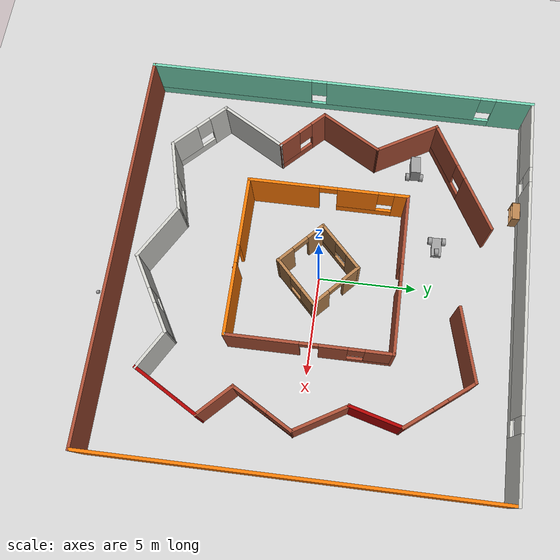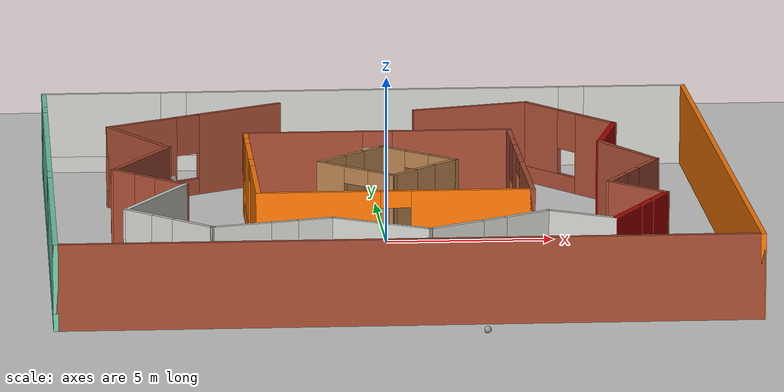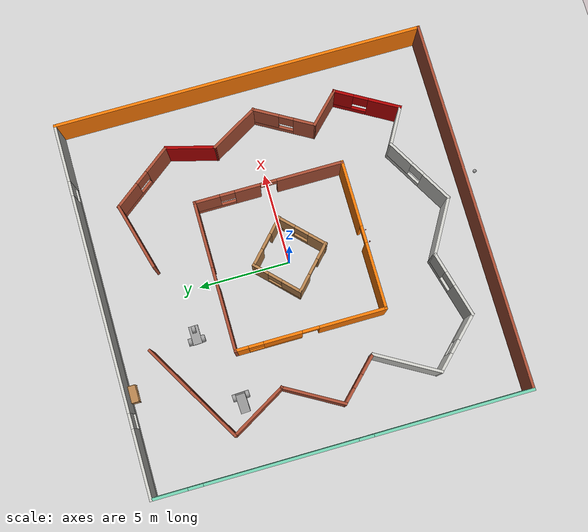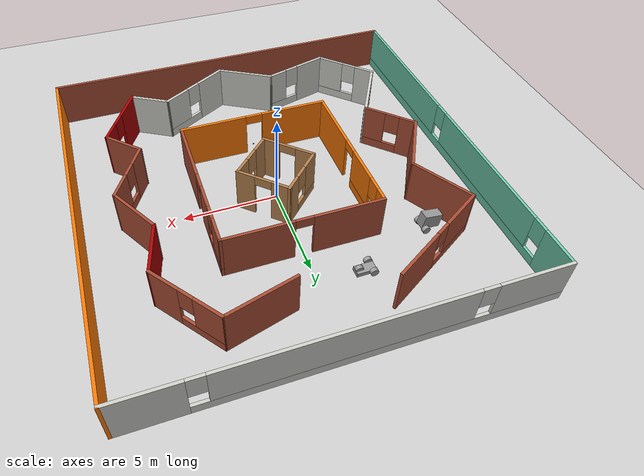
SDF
<sdf version="1.6">
 <world name="default">
  <plugin name="welcome" filename="libwelcome.so"/>
  <light name="sun" type="directional">
   <pose>0 0 10 0 -0 0</pose>
   <diffuse>0.8 0.8 0.8 1</diffuse>
   <specular>0.2 0.2 0.2 1</specular>
   <attenuation>
    <range>1000</range>
    <constant>0.9</constant>
    <linear>0.01</linear>
    <quadratic>0.001</quadratic>
   </attenuation>
   <direction>-0.5 0.1 -0.9</direction>
  </light>
  <model name="ground_plane">
   <static>1</static>
   <link name="link">
    <collision name="collision">
     <geometry><plane><normal>0 0 1</normal><size>100 100</size></plane></geometry>
     <surface><friction><ode><mu>100</mu><mu2>50</mu2></ode></friction></surface>
    </collision>
    <visual name="visual">
     <cast_shadows>0</cast_shadows>
     <geometry><plane><normal>0 0 1</normal><size>100 100</size></plane></geometry>
     <material>
      <script><uri>file://media/materials/scripts/gazebo.material</uri><name>Gazebo/Grey</name></script>
     </material>
    </visual>
   </link>
  </model>
  <gravity>0 0 -9.8</gravity>
  <magnetic_field>6e-06 2.3e-05 -4.2e-05</magnetic_field>
  <atmosphere type="adiabatic"/>
  <physics name="default_physics" default="0" type="ode">
   <max_step_size>0.001</max_step_size>
   <real_time_factor>1</real_time_factor>
   <real_time_update_rate>1000</real_time_update_rate>
  </physics>
  <scene><ambient>0.4 0.4 0.4 1</ambient><background>0.7 0.7 0.7 1</background><shadows>1</shadows></scene>
  <spherical_coordinates>
   <surface_model>EARTH_WGS84</surface_model>
   <latitude_deg>0</latitude_deg>
   <longitude_deg>0</longitude_deg>
   <elevation>0</elevation>
   <heading_deg>0</heading_deg>
  </spherical_coordinates>
  <model name="building">
   <link name="Wall_44">
    <collision name="Wall_44_Collision">
     <geometry><box><size>20.15 0.15 2.5</size></box></geometry>
     <pose>0 0 1.25 0 -0 0</pose>
    </collision>
    <visual name="Wall_44_Visual">
     <pose>0 0 1.25 0 -0 0</pose>
     <geometry><box><size>20.15 0.15 2.5</size></box></geometry>
     <material>
      <script><uri>file://media/materials/scripts/gazebo.material</uri><name>Gazebo/Bricks</name></script>
      <ambient>0.760784 0.662745 0.627451 1</ambient>
     </material>
     <meta><layer>0</layer></meta>
    </visual>
    <pose>0 -10 0 0 -0 0</pose>
   </link>
   <link name="Wall_45">
    <collision name="Wall_45_Collision">
     <geometry><box><size>20.15 0.15 2.5</size></box></geometry>
     <pose>0 0 1.25 0 -0 0</pose>
    </collision>
    <visual name="Wall_45_Visual">
     <pose>0 0 1.25 0 -0 0</pose>
     <geometry><box><size>20.15 0.15 2.5</size></box></geometry>
     <material>
      <script><uri>file://media/materials/scripts/gazebo.material</uri><name>Gazebo/Grey</name></script>
      <ambient>0.996078 0.47451 0.0196078 1</ambient>
     </material>
     <meta><layer>0</layer></meta>
    </visual>
    <pose>10 0 0 0 -0 1.5708</pose>
   </link>
   <link name="Wall_46">
    <pose>0 10 0 0 -0 3.14159</pose>
    <visual name="Wall_46_Visual_0">
     <pose>-8.48027 0 1.25 0 -0 0</pose>
     <geometry><box><size>3.18945 0.15 2.5</size></box></geometry>
     <material>
      <script><uri>file://media/materials/scripts/gazebo.material</uri><name>Gazebo/CeilingTiled</name></script>
      <ambient>0.333333 0 1 1</ambient>
     </material>
     <meta><layer>0</layer></meta>
    </visual>
    <collision name="Wall_46_Collision_0">
     <geometry><box><size>3.18945 0.15 2.5</size></box></geometry>
     <pose>-8.48027 0 1.25 0 -0 0</pose>
    </collision>
    <visual name="Wall_46_Visual_1">
     <pose>1.59473 0 0.25 0 -0 0</pose>
     <geometry><box><size>16.9605 0.15 0.5</size></box></geometry>
     <material>
      <script><uri>file://media/materials/scripts/gazebo.material</uri><name>Gazebo/CeilingTiled</name></script>
      <ambient>0.333333 0 1 1</ambient>
     </material>
     <meta><layer>0</layer></meta>
    </visual>
    <collision name="Wall_46_Collision_1">
     <geometry><box><size>16.9605 0.15 0.5</size></box></geometry>
     <pose>1.59473 0 0.25 0 -0 0</pose>
    </collision>
    <visual name="Wall_46_Visual_2">
     <pose>-0.261101 0 1.5 0 -0 0</pose>
     <geometry><box><size>11.6489 0.15 2</size></box></geometry>
     <material>
      <script><uri>file://media/materials/scripts/gazebo.material</uri><name>Gazebo/CeilingTiled</name></script>
      <ambient>0.333333 0 1 1</ambient>
     </material>
     <meta><layer>0</layer></meta>
    </visual>
    <collision name="Wall_46_Collision_2">
     <geometry><box><size>11.6489 0.15 2</size></box></geometry>
     <pose>-0.261101 0 1.5 0 -0 0</pose>
    </collision>
    <visual name="Wall_46_Visual_3">
     <pose>8.21917 0 1.5 0 -0 0</pose>
     <geometry><box><size>3.71165 0.15 2</size></box></geometry>
     <material>
      <script><uri>file://media/materials/scripts/gazebo.material</uri><name>Gazebo/CeilingTiled</name></script>
      <ambient>0.333333 0 1 1</ambient>
     </material>
     <meta><layer>0</layer></meta>
    </visual>
    <collision name="Wall_46_Collision_3">
     <geometry><box><size>3.71165 0.15 2</size></box></geometry>
     <pose>8.21917 0 1.5 0 -0 0</pose>
    </collision>
    <visual name="Wall_46_Visual_4">
     <pose>-6.48555 0 1.9 0 -0 0</pose>
     <geometry><box><size>0.8 0.15 1.2</size></box></geometry>
     <material>
      <script><uri>file://media/materials/scripts/gazebo.material</uri><name>Gazebo/CeilingTiled</name></script>
      <ambient>0.333333 0 1 1</ambient>
     </material>
     <meta><layer>0</layer></meta>
    </visual>
    <collision name="Wall_46_Collision_4">
     <geometry><box><size>0.8 0.15 1.2</size></box></geometry>
     <pose>-6.48555 0 1.9 0 -0 0</pose>
    </collision>
    <visual name="Wall_46_Visual_5">
     <pose>5.96335 0 1.9 0 -0 0</pose>
     <geometry><box><size>0.8 0.15 1.2</size></box></geometry>
     <material>
      <script><uri>file://media/materials/scripts/gazebo.material</uri><name>Gazebo/CeilingTiled</name></script>
      <ambient>0.333333 0 1 1</ambient>
     </material>
     <meta><layer>0</layer></meta>
    </visual>
    <collision name="Wall_46_Collision_5">
     <geometry><box><size>0.8 0.15 1.2</size></box></geometry>
     <pose>5.96335 0 1.9 0 -0 0</pose>
    </collision>
   </link>
   <link name="Wall_47">
    <pose>-10 0 0 0 0 -1.5708</pose>
    <visual name="Wall_47_Visual_0">
     <pose>-9.08483 0 1.25 0 -0 0</pose>
     <geometry><box><size>1.98033 0.15 2.5</size></box></geometry>
     <material>
      <script><uri>file://media/materials/scripts/gazebo.material</uri><name>Gazebo/Grey</name></script>
      <ambient>0.435294 0.796078 0.67451 1</ambient>
     </material>
     <meta><layer>0</layer></meta>
    </visual>
    <collision name="Wall_47_Collision_0">
     <geometry><box><size>1.98033 0.15 2.5</size></box></geometry>
     <pose>-9.08483 0 1.25 0 -0 0</pose>
    </collision>
    <visual name="Wall_47_Visual_1">
     <pose>0.990168 0 0.25 0 -0 0</pose>
     <geometry><box><size>18.1697 0.15 0.5</size></box></geometry>
     <material>
      <script><uri>file://media/materials/scripts/gazebo.material</uri><name>Gazebo/Grey</name></script>
      <ambient>0.435294 0.796078 0.67451 1</ambient>
     </material>
     <meta><layer>0</layer></meta>
    </visual>
    <collision name="Wall_47_Collision_1">
     <geometry><box><size>18.1697 0.15 0.5</size></box></geometry>
     <pose>0.990168 0 0.25 0 -0 0</pose>
    </collision>
    <visual name="Wall_47_Visual_2">
     <pose>-3.25243 0 1.5 0 -0 0</pose>
     <geometry><box><size>8.08447 0.15 2</size></box></geometry>
     <material>
      <script><uri>file://media/materials/scripts/gazebo.material</uri><name>Gazebo/Grey</name></script>
      <ambient>0.435294 0.796078 0.67451 1</ambient>
     </material>
     <meta><layer>0</layer></meta>
    </visual>
    <collision name="Wall_47_Collision_2">
     <geometry><box><size>8.08447 0.15 2</size></box></geometry>
     <pose>-3.25243 0 1.5 0 -0 0</pose>
    </collision>
    <visual name="Wall_47_Visual_3">
     <pose>5.8324 0 1.5 0 -0 0</pose>
     <geometry><box><size>8.4852 0.15 2</size></box></geometry>
     <material>
      <script><uri>file://media/materials/scripts/gazebo.material</uri><name>Gazebo/Grey</name></script>
      <ambient>0.435294 0.796078 0.67451 1</ambient>
     </material>
     <meta><layer>0</layer></meta>
    </visual>
    <collision name="Wall_47_Collision_3">
     <geometry><box><size>8.4852 0.15 2</size></box></geometry>
     <pose>5.8324 0 1.5 0 -0 0</pose>
    </collision>
    <visual name="Wall_47_Visual_4">
     <pose>-7.69466 0 1.9 0 -0 0</pose>
     <geometry><box><size>0.8 0.15 1.2</size></box></geometry>
     <material>
      <script><uri>file://media/materials/scripts/gazebo.material</uri><name>Gazebo/Grey</name></script>
      <ambient>0.435294 0.796078 0.67451 1</ambient>
     </material>
     <meta><layer>0</layer></meta>
    </visual>
    <collision name="Wall_47_Collision_4">
     <geometry><box><size>0.8 0.15 1.2</size></box></geometry>
     <pose>-7.69466 0 1.9 0 -0 0</pose>
    </collision>
    <visual name="Wall_47_Visual_5">
     <pose>1.1898 0 1.9 0 -0 0</pose>
     <geometry><box><size>0.8 0.15 1.2</size></box></geometry>
     <material>
      <script><uri>file://media/materials/scripts/gazebo.material</uri><name>Gazebo/Grey</name></script>
      <ambient>0.435294 0.796078 0.67451 1</ambient>
     </material>
     <meta><layer>0</layer></meta>
    </visual>
    <collision name="Wall_47_Collision_5">
     <geometry><box><size>0.8 0.15 1.2</size></box></geometry>
     <pose>1.1898 0 1.9 0 -0 0</pose>
    </collision>
   </link>
   <link name="Wall_49">
    <pose>-4 0 0 0 0 -1.5708</pose>
    <visual name="Wall_49_Visual_0">
     <pose>-3.69081 0 1.25 0 -0 0</pose>
     <geometry><box><size>0.768371 0.15 2.5</size></box></geometry>
     <material>
      <script><uri>file://media/materials/scripts/gazebo.material</uri><name>Gazebo/Grey</name></script>
      <ambient>0.996078 0.47451 0.0196078 1</ambient>
     </material>
     <meta><layer>0</layer></meta>
    </visual>
    <collision name="Wall_49_Collision_0">
     <geometry><box><size>0.768371 0.15 2.5</size></box></geometry>
     <pose>-3.69081 0 1.25 0 -0 0</pose>
    </collision>
    <visual name="Wall_49_Visual_1">
     <pose>2.2625 0 1.25 0 -0 0</pose>
     <geometry><box><size>3.625 0.15 2.5</size></box></geometry>
     <material>
      <script><uri>file://media/materials/scripts/gazebo.material</uri><name>Gazebo/Grey</name></script>
      <ambient>0.996078 0.47451 0.0196078 1</ambient>
     </material>
     <meta><layer>0</layer></meta>
    </visual>
    <collision name="Wall_49_Collision_1">
     <geometry><box><size>3.625 0.15 2.5</size></box></geometry>
     <pose>2.2625 0 1.25 0 -0 0</pose>
    </collision>
    <visual name="Wall_49_Visual_2">
     <pose>-1.87831 0 0.25 0 -0 0</pose>
     <geometry><box><size>2.85663 0.15 0.5</size></box></geometry>
     <material>
      <script><uri>file://media/materials/scripts/gazebo.material</uri><name>Gazebo/Grey</name></script>
      <ambient>0.996078 0.47451 0.0196078 1</ambient>
     </material>
     <meta><layer>0</layer></meta>
    </visual>
    <collision name="Wall_49_Collision_2">
     <geometry><box><size>2.85663 0.15 0.5</size></box></geometry>
     <pose>-1.87831 0 0.25 0 -0 0</pose>
    </collision>
    <visual name="Wall_49_Visual_3">
     <pose>-1.47831 0 1.5 0 -0 0</pose>
     <geometry><box><size>2.05663 0.15 2</size></box></geometry>
     <material>
      <script><uri>file://media/materials/scripts/gazebo.material</uri><name>Gazebo/Grey</name></script>
      <ambient>0.996078 0.47451 0.0196078 1</ambient>
     </material>
     <meta><layer>0</layer></meta>
    </visual>
    <collision name="Wall_49_Collision_3">
     <geometry><box><size>2.05663 0.15 2</size></box></geometry>
     <pose>-1.47831 0 1.5 0 -0 0</pose>
    </collision>
    <visual name="Wall_49_Visual_4">
     <pose>-2.90663 0 1.9 0 -0 0</pose>
     <geometry><box><size>0.8 0.15 1.2</size></box></geometry>
     <material>
      <script><uri>file://media/materials/scripts/gazebo.material</uri><name>Gazebo/Grey</name></script>
      <ambient>0.996078 0.47451 0.0196078 1</ambient>
     </material>
     <meta><layer>0</layer></meta>
    </visual>
    <collision name="Wall_49_Collision_4">
     <geometry><box><size>0.8 0.15 1.2</size></box></geometry>
     <pose>-2.90663 0 1.9 0 -0 0</pose>
    </collision>
    <visual name="Wall_49_Visual_5">
     <pose>0 0 2.25 0 -0 0</pose>
     <geometry><box><size>0.9 0.15 0.5</size></box></geometry>
     <material>
      <script><uri>file://media/materials/scripts/gazebo.material</uri><name>Gazebo/Grey</name></script>
      <ambient>0.996078 0.47451 0.0196078 1</ambient>
     </material>
     <meta><layer>0</layer></meta>
    </visual>
    <collision name="Wall_49_Collision_5">
     <geometry><box><size>0.9 0.15 0.5</size></box></geometry>
     <pose>0 0 2.25 0 -0 0</pose>
    </collision>
   </link>
   <link name="Wall_50">
    <pose>0 -4 0 0 -0 0</pose>
    <visual name="Wall_50_Visual_0">
     <pose>-2.2625 0 1.25 0 -0 0</pose>
     <geometry><box><size>3.625 0.15 2.5</size></box></geometry>
     <material>
      <script><uri>file://media/materials/scripts/gazebo.material</uri><name>Gazebo/Grey</name></script>
      <ambient>0.996078 0.47451 0.0196078 1</ambient>
     </material>
     <meta><layer>0</layer></meta>
    </visual>
    <collision name="Wall_50_Collision_0">
     <geometry><box><size>3.625 0.15 2.5</size></box></geometry>
     <pose>-2.2625 0 1.25 0 -0 0</pose>
    </collision>
    <visual name="Wall_50_Visual_1">
     <pose>2.2625 0 1.25 0 -0 0</pose>
     <geometry><box><size>3.625 0.15 2.5</size></box></geometry>
     <material>
      <script><uri>file://media/materials/scripts/gazebo.material</uri><name>Gazebo/Grey</name></script>
      <ambient>0.996078 0.47451 0.0196078 1</ambient>
     </material>
     <meta><layer>0</layer></meta>
    </visual>
    <collision name="Wall_50_Collision_1">
     <geometry><box><size>3.625 0.15 2.5</size></box></geometry>
     <pose>2.2625 0 1.25 0 -0 0</pose>
    </collision>
    <visual name="Wall_50_Visual_2">
     <pose>0 0 2.25 0 -0 0</pose>
     <geometry><box><size>0.9 0.15 0.5</size></box></geometry>
     <material>
      <script><uri>file://media/materials/scripts/gazebo.material</uri><name>Gazebo/Grey</name></script>
      <ambient>0.996078 0.47451 0.0196078 1</ambient>
     </material>
     <meta><layer>0</layer></meta>
    </visual>
    <collision name="Wall_50_Collision_2">
     <geometry><box><size>0.9 0.15 0.5</size></box></geometry>
     <pose>0 0 2.25 0 -0 0</pose>
    </collision>
   </link>
   <link name="Wall_51">
    <collision name="Wall_51_Collision">
     <geometry><box><size>0.15 0.15 2.5</size></box></geometry>
     <pose>0 0 1.25 0 -0 0</pose>
    </collision>
    <visual name="Wall_51_Visual">
     <pose>0 0 1.25 0 -0 0</pose>
     <geometry><box><size>0.15 0.15 2.5</size></box></geometry>
     <material>
      <script><uri>file://media/materials/scripts/gazebo.material</uri><name>Gazebo/CeilingTiled</name></script>
      <ambient>0.435294 0.796078 0.67451 1</ambient>
     </material>
     <meta><layer>0</layer></meta>
    </visual>
    <pose>4 -4 0 0 -0 0</pose>
   </link>
   <link name="Wall_52">
    <pose>4 0 0 0 -0 1.5708</pose>
    <visual name="Wall_52_Visual_0">
     <pose>-2.2608 0 1.25 0 -0 0</pose>
     <geometry><box><size>3.6284 0.15 2.5</size></box></geometry>
     <material>
      <script><uri>file://media/materials/scripts/gazebo.material</uri><name>Gazebo/Bricks</name></script>
      <ambient>1 1 1 1</ambient>
     </material>
     <meta><layer>0</layer></meta>
    </visual>
    <collision name="Wall_52_Collision_0">
     <geometry><box><size>3.6284 0.15 2.5</size></box></geometry>
     <pose>-2.2608 0 1.25 0 -0 0</pose>
    </collision>
    <visual name="Wall_52_Visual_1">
     <pose>1.14751 0 1.25 0 -0 0</pose>
     <geometry><box><size>1.38822 0.15 2.5</size></box></geometry>
     <material>
      <script><uri>file://media/materials/scripts/gazebo.material</uri><name>Gazebo/Bricks</name></script>
      <ambient>1 1 1 1</ambient>
     </material>
     <meta><layer>0</layer></meta>
    </visual>
    <collision name="Wall_52_Collision_1">
     <geometry><box><size>1.38822 0.15 2.5</size></box></geometry>
     <pose>1.14751 0 1.25 0 -0 0</pose>
    </collision>
    <visual name="Wall_52_Visual_2">
     <pose>2.95831 0 0.25 0 -0 0</pose>
     <geometry><box><size>2.23338 0.15 0.5</size></box></geometry>
     <material>
      <script><uri>file://media/materials/scripts/gazebo.material</uri><name>Gazebo/Bricks</name></script>
      <ambient>1 1 1 1</ambient>
     </material>
     <meta><layer>0</layer></meta>
    </visual>
    <collision name="Wall_52_Collision_2">
     <geometry><box><size>2.23338 0.15 0.5</size></box></geometry>
     <pose>2.95831 0 0.25 0 -0 0</pose>
    </collision>
    <visual name="Wall_52_Visual_3">
     <pose>3.35831 0 1.5 0 -0 0</pose>
     <geometry><box><size>1.43338 0.15 2</size></box></geometry>
     <material>
      <script><uri>file://media/materials/scripts/gazebo.material</uri><name>Gazebo/Bricks</name></script>
      <ambient>1 1 1 1</ambient>
     </material>
     <meta><layer>0</layer></meta>
    </visual>
    <collision name="Wall_52_Collision_3">
     <geometry><box><size>1.43338 0.15 2</size></box></geometry>
     <pose>3.35831 0 1.5 0 -0 0</pose>
    </collision>
    <visual name="Wall_52_Visual_4">
     <pose>2.24162 0 1.9 0 -0 0</pose>
     <geometry><box><size>0.8 0.15 1.2</size></box></geometry>
     <material>
      <script><uri>file://media/materials/scripts/gazebo.material</uri><name>Gazebo/Bricks</name></script>
      <ambient>1 1 1 1</ambient>
     </material>
     <meta><layer>0</layer></meta>
    </visual>
    <collision name="Wall_52_Collision_4">
     <geometry><box><size>0.8 0.15 1.2</size></box></geometry>
     <pose>2.24162 0 1.9 0 -0 0</pose>
    </collision>
    <visual name="Wall_52_Visual_5">
     <pose>0.003404 0 2.25 0 -0 0</pose>
     <geometry><box><size>0.9 0.15 0.5</size></box></geometry>
     <material>
      <script><uri>file://media/materials/scripts/gazebo.material</uri><name>Gazebo/Bricks</name></script>
      <ambient>1 1 1 1</ambient>
     </material>
     <meta><layer>0</layer></meta>
    </visual>
    <collision name="Wall_52_Collision_5">
     <geometry><box><size>0.9 0.15 0.5</size></box></geometry>
     <pose>0.003404 0 2.25 0 -0 0</pose>
    </collision>
   </link>
   <link name="Wall_54">
    <pose>0 4 0 0 -0 3.14159</pose>
    <visual name="Wall_54_Visual_0">
     <pose>-2.2625 0 1.25 0 -0 0</pose>
     <geometry><box><size>3.625 0.15 2.5</size></box></geometry>
     <material>
      <script><uri>file://media/materials/scripts/gazebo.material</uri><name>Gazebo/Bricks</name></script>
      <ambient>1 1 1 1</ambient>
     </material>
     <meta><layer>0</layer></meta>
    </visual>
    <collision name="Wall_54_Collision_0">
     <geometry><box><size>3.625 0.15 2.5</size></box></geometry>
     <pose>-2.2625 0 1.25 0 -0 0</pose>
    </collision>
    <visual name="Wall_54_Visual_1">
     <pose>2.2625 0 1.25 0 -0 0</pose>
     <geometry><box><size>3.625 0.15 2.5</size></box></geometry>
     <material>
      <script><uri>file://media/materials/scripts/gazebo.material</uri><name>Gazebo/Bricks</name></script>
      <ambient>1 1 1 1</ambient>
     </material>
     <meta><layer>0</layer></meta>
    </visual>
    <collision name="Wall_54_Collision_1">
     <geometry><box><size>3.625 0.15 2.5</size></box></geometry>
     <pose>2.2625 0 1.25 0 -0 0</pose>
    </collision>
    <visual name="Wall_54_Visual_2">
     <pose>0 0 2.25 0 -0 0</pose>
     <geometry><box><size>0.9 0.15 0.5</size></box></geometry>
     <material>
      <script><uri>file://media/materials/scripts/gazebo.material</uri><name>Gazebo/Bricks</name></script>
      <ambient>1 1 1 1</ambient>
     </material>
     <meta><layer>0</layer></meta>
    </visual>
    <collision name="Wall_54_Collision_2">
     <geometry><box><size>0.9 0.15 0.5</size></box></geometry>
     <pose>0 0 2.25 0 -0 0</pose>
    </collision>
   </link>
   <link name="Wall_58">
    <pose>-0.981304 0.947415 0 0 0 -2.36683</pose>
    <visual name="Wall_58_Visual_0">
     <pose>-0.975073 0 1.25 0 -0 0</pose>
     <geometry><box><size>0.954837 0.15 2.5</size></box></geometry>
     <material>
      <script><uri>file://media/materials/scripts/gazebo.material</uri><name>Gazebo/Wood</name></script>
      <ambient>0.333333 0 1 1</ambient>
     </material>
     <meta><layer>0</layer></meta>
    </visual>
    <collision name="Wall_58_Collision_0">
     <geometry><box><size>0.954837 0.15 2.5</size></box></geometry>
     <pose>-0.975073 0 1.25 0 -0 0</pose>
    </collision>
    <visual name="Wall_58_Visual_1">
     <pose>0.477419 0 0.25 0 -0 0</pose>
     <geometry><box><size>1.95015 0.15 0.5</size></box></geometry>
     <material>
      <script><uri>file://media/materials/scripts/gazebo.material</uri><name>Gazebo/Wood</name></script>
      <ambient>0.333333 0 1 1</ambient>
     </material>
     <meta><layer>0</layer></meta>
    </visual>
    <collision name="Wall_58_Collision_1">
     <geometry><box><size>1.95015 0.15 0.5</size></box></geometry>
     <pose>0.477419 0 0.25 0 -0 0</pose>
    </collision>
    <visual name="Wall_58_Visual_2">
     <pose>0.877419 0 1.5 0 -0 0</pose>
     <geometry><box><size>1.15015 0.15 2</size></box></geometry>
     <material>
      <script><uri>file://media/materials/scripts/gazebo.material</uri><name>Gazebo/Wood</name></script>
      <ambient>0.333333 0 1 1</ambient>
     </material>
     <meta><layer>0</layer></meta>
    </visual>
    <collision name="Wall_58_Collision_2">
     <geometry><box><size>1.15015 0.15 2</size></box></geometry>
     <pose>0.877419 0 1.5 0 -0 0</pose>
    </collision>
    <visual name="Wall_58_Visual_3">
     <pose>-0.097655 0 1.9 0 -0 0</pose>
     <geometry><box><size>0.8 0.15 1.2</size></box></geometry>
     <material>
      <script><uri>file://media/materials/scripts/gazebo.material</uri><name>Gazebo/Wood</name></script>
      <ambient>0.333333 0 1 1</ambient>
     </material>
     <meta><layer>0</layer></meta>
    </visual>
    <collision name="Wall_58_Collision_3">
     <geometry><box><size>0.8 0.15 1.2</size></box></geometry>
     <pose>-0.097655 0 1.9 0 -0 0</pose>
    </collision>
   </link>
   <link name="Wall_59">
    <pose>-0.941632 -0.998316 0 0 0 -0.755492</pose>
    <visual name="Wall_59_Visual_0">
     <pose>-0.952898 0 1.25 0 -0 0</pose>
     <geometry><box><size>1.05767 0.15 2.5</size></box></geometry>
     <material>
      <script><uri>file://media/materials/scripts/gazebo.material</uri><name>Gazebo/Wood</name></script>
      <ambient>0.333333 0 1 1</ambient>
     </material>
     <meta><layer>0</layer></meta>
    </visual>
    <collision name="Wall_59_Collision_0">
     <geometry><box><size>1.05767 0.15 2.5</size></box></geometry>
     <pose>-0.952898 0 1.25 0 -0 0</pose>
    </collision>
    <visual name="Wall_59_Visual_1">
     <pose>0.978835 0 1.25 0 -0 0</pose>
     <geometry><box><size>1.0058 0.15 2.5</size></box></geometry>
     <material>
      <script><uri>file://media/materials/scripts/gazebo.material</uri><name>Gazebo/Wood</name></script>
      <ambient>0.333333 0 1 1</ambient>
     </material>
     <meta><layer>0</layer></meta>
    </visual>
    <collision name="Wall_59_Collision_1">
     <geometry><box><size>1.0058 0.15 2.5</size></box></geometry>
     <pose>0.978835 0 1.25 0 -0 0</pose>
    </collision>
    <visual name="Wall_59_Visual_2">
     <pose>0.025937 0 2.25 0 -0 0</pose>
     <geometry><box><size>0.9 0.15 0.5</size></box></geometry>
     <material>
      <script><uri>file://media/materials/scripts/gazebo.material</uri><name>Gazebo/Wood</name></script>
      <ambient>0.333333 0 1 1</ambient>
     </material>
     <meta><layer>0</layer></meta>
    </visual>
    <collision name="Wall_59_Collision_2">
     <geometry><box><size>0.9 0.15 0.5</size></box></geometry>
     <pose>0.025937 0 2.25 0 -0 0</pose>
    </collision>
   </link>
   <link name="Wall_60">
    <pose>1.04341 -0.990461 0 0 -0 0.779305</pose>
    <visual name="Wall_60_Visual_0">
     <pose>-0.909688 0 1.25 0 -0 0</pose>
     <geometry><box><size>1.09783 0.15 2.5</size></box></geometry>
     <material>
      <script><uri>file://media/materials/scripts/gazebo.material</uri><name>Gazebo/Wood</name></script>
      <ambient>0.333333 0 1 1</ambient>
     </material>
     <meta><layer>0</layer></meta>
    </visual>
    <collision name="Wall_60_Collision_0">
     <geometry><box><size>1.09783 0.15 2.5</size></box></geometry>
     <pose>-0.909688 0 1.25 0 -0 0</pose>
    </collision>
    <visual name="Wall_60_Visual_1">
     <pose>0.548916 0 0.25 0 -0 0</pose>
     <geometry><box><size>1.81938 0.15 0.5</size></box></geometry>
     <material>
      <script><uri>file://media/materials/scripts/gazebo.material</uri><name>Gazebo/Wood</name></script>
      <ambient>0.333333 0 1 1</ambient>
     </material>
     <meta><layer>0</layer></meta>
    </visual>
    <collision name="Wall_60_Collision_1">
     <geometry><box><size>1.81938 0.15 0.5</size></box></geometry>
     <pose>0.548916 0 0.25 0 -0 0</pose>
    </collision>
    <visual name="Wall_60_Visual_2">
     <pose>0.948916 0 1.5 0 -0 0</pose>
     <geometry><box><size>1.01938 0.15 2</size></box></geometry>
     <material>
      <script><uri>file://media/materials/scripts/gazebo.material</uri><name>Gazebo/Wood</name></script>
      <ambient>0.333333 0 1 1</ambient>
     </material>
     <meta><layer>0</layer></meta>
    </visual>
    <collision name="Wall_60_Collision_2">
     <geometry><box><size>1.01938 0.15 2</size></box></geometry>
     <pose>0.948916 0 1.5 0 -0 0</pose>
    </collision>
    <visual name="Wall_60_Visual_3">
     <pose>0.039229 0 1.9 0 -0 0</pose>
     <geometry><box><size>0.8 0.15 1.2</size></box></geometry>
     <material>
      <script><uri>file://media/materials/scripts/gazebo.material</uri><name>Gazebo/Wood</name></script>
      <ambient>0.333333 0 1 1</ambient>
     </material>
     <meta><layer>0</layer></meta>
    </visual>
    <collision name="Wall_60_Collision_3">
     <geometry><box><size>0.8 0.15 1.2</size></box></geometry>
     <pose>0.039229 0 1.9 0 -0 0</pose>
    </collision>
   </link>
   <link name="Wall_61">
    <pose>1.02035 0.946475 0 0 -0 2.38929</pose>
    <visual name="Wall_61_Visual_0">
     <pose>-0.968361 0 1.25 0 -0 0</pose>
     <geometry><box><size>1.03644 0.15 2.5</size></box></geometry>
     <material>
      <script><uri>file://media/materials/scripts/gazebo.material</uri><name>Gazebo/Wood</name></script>
      <ambient>0.333333 0 1 1</ambient>
     </material>
     <meta><layer>0</layer></meta>
    </visual>
    <collision name="Wall_61_Collision_0">
     <geometry><box><size>1.03644 0.15 2.5</size></box></geometry>
     <pose>-0.968361 0 1.25 0 -0 0</pose>
    </collision>
    <visual name="Wall_61_Visual_1">
     <pose>0.968218 0 1.25 0 -0 0</pose>
     <geometry><box><size>1.03672 0.15 2.5</size></box></geometry>
     <material>
      <script><uri>file://media/materials/scripts/gazebo.material</uri><name>Gazebo/Wood</name></script>
      <ambient>0.333333 0 1 1</ambient>
     </material>
     <meta><layer>0</layer></meta>
    </visual>
    <collision name="Wall_61_Collision_1">
     <geometry><box><size>1.03672 0.15 2.5</size></box></geometry>
     <pose>0.968218 0 1.25 0 -0 0</pose>
    </collision>
    <visual name="Wall_61_Visual_2">
     <pose>-0.000142 0 2.25 0 -0 0</pose>
     <geometry><box><size>0.9 0.15 0.5</size></box></geometry>
     <material>
      <script><uri>file://media/materials/scripts/gazebo.material</uri><name>Gazebo/Wood</name></script>
      <ambient>0.333333 0 1 1</ambient>
     </material>
     <meta><layer>0</layer></meta>
    </visual>
    <collision name="Wall_61_Collision_2">
     <geometry><box><size>0.9 0.15 0.5</size></box></geometry>
     <pose>-0.000142 0 2.25 0 -0 0</pose>
    </collision>
   </link>
   <link name="Wall_63">
    <pose>-5.44703 6.66103 0 0 0 -2.61799</pose>
    <visual name="Wall_63_Visual_0">
     <pose>-1.62657 0 1.25 0 -0 0</pose>
     <geometry><box><size>2.99687 0.15 2.5</size></box></geometry>
     <material>
      <script><uri>file://media/materials/scripts/gazebo.material</uri><name>Gazebo/Bricks</name></script>
      <ambient>0.666667 0 0 1</ambient>
     </material>
     <meta><layer>0</layer></meta>
    </visual>
    <collision name="Wall_63_Collision_0">
     <geometry><box><size>2.99687 0.15 2.5</size></box></geometry>
     <pose>-1.62657 0 1.25 0 -0 0</pose>
    </collision>
    <visual name="Wall_63_Visual_1">
     <pose>1.49843 0 0.25 0 -0 0</pose>
     <geometry><box><size>3.25313 0.15 0.5</size></box></geometry>
     <material>
      <script><uri>file://media/materials/scripts/gazebo.material</uri><name>Gazebo/Bricks</name></script>
      <ambient>0.666667 0 0 1</ambient>
     </material>
     <meta><layer>0</layer></meta>
    </visual>
    <collision name="Wall_63_Collision_1">
     <geometry><box><size>3.25313 0.15 0.5</size></box></geometry>
     <pose>1.49843 0 0.25 0 -0 0</pose>
    </collision>
    <visual name="Wall_63_Visual_2">
     <pose>1.89843 0 1.5 0 -0 0</pose>
     <geometry><box><size>2.45314 0.15 2</size></box></geometry>
     <material>
      <script><uri>file://media/materials/scripts/gazebo.material</uri><name>Gazebo/Bricks</name></script>
      <ambient>0.666667 0 0 1</ambient>
     </material>
     <meta><layer>0</layer></meta>
    </visual>
    <collision name="Wall_63_Collision_2">
     <geometry><box><size>2.45314 0.15 2</size></box></geometry>
     <pose>1.89843 0 1.5 0 -0 0</pose>
    </collision>
    <visual name="Wall_63_Visual_3">
     <pose>0.271865 0 1.9 0 -0 0</pose>
     <geometry><box><size>0.8 0.15 1.2</size></box></geometry>
     <material>
      <script><uri>file://media/materials/scripts/gazebo.material</uri><name>Gazebo/Bricks</name></script>
      <ambient>0.666667 0 0 1</ambient>
     </material>
     <meta><layer>0</layer></meta>
    </visual>
    <collision name="Wall_63_Collision_3">
     <geometry><box><size>0.8 0.15 1.2</size></box></geometry>
     <pose>0.271865 0 1.9 0 -0 0</pose>
    </collision>
   </link>
   <link name="Wall_64">
    <collision name="Wall_64_Collision">
     <geometry><box><size>3.5 0.15 2.5</size></box></geometry>
     <pose>0 0 1.25 0 -0 0</pose>
    </collision>
    <visual name="Wall_64_Visual">
     <pose>0 0 1.25 0 -0 0</pose>
     <geometry><box><size>3.5 0.15 2.5</size></box></geometry>
     <material>
      <script><uri>file://media/materials/scripts/gazebo.material</uri><name>Gazebo/Bricks</name></script>
      <ambient>0.666667 0 0 1</ambient>
     </material>
     <meta><layer>0</layer></meta>
    </visual>
    <pose>-7.25091 3.68544 0 0 0 -1.0472</pose>
   </link>
   <link name="Wall_65">
    <collision name="Wall_65_Collision">
     <geometry><box><size>3.5 0.15 2.5</size></box></geometry>
     <pose>0 0 1.25 0 -0 0</pose>
    </collision>
    <visual name="Wall_65_Visual">
     <pose>0 0 1.25 0 -0 0</pose>
     <geometry><box><size>3.5 0.15 2.5</size></box></geometry>
     <material>
      <script><uri>file://media/materials/scripts/gazebo.material</uri><name>Gazebo/Bricks</name></script>
      <ambient>0.666667 0 0 1</ambient>
     </material>
     <meta><layer>0</layer></meta>
    </visual>
    <pose>-7.25091 0.78425 0 0 0 -2.0944</pose>
   </link>
   <link name="Wall_66">
    <pose>-7.08078 -1.67397 0 0 0 -0.785398</pose>
    <visual name="Wall_66_Visual_0">
     <pose>-1.01765 0 1.25 0 -0 0</pose>
     <geometry><box><size>0.964702 0.15 2.5</size></box></geometry>
     <material>
      <script><uri>file://media/materials/scripts/gazebo.material</uri><name>Gazebo/Bricks</name></script>
      <ambient>0.666667 0 0 1</ambient>
     </material>
     <meta><layer>0</layer></meta>
    </visual>
    <collision name="Wall_66_Collision_0">
     <geometry><box><size>0.964702 0.15 2.5</size></box></geometry>
     <pose>-1.01765 0 1.25 0 -0 0</pose>
    </collision>
    <visual name="Wall_66_Visual_1">
     <pose>0.482351 0 0.25 0 -0 0</pose>
     <geometry><box><size>2.0353 0.15 0.5</size></box></geometry>
     <material>
      <script><uri>file://media/materials/scripts/gazebo.material</uri><name>Gazebo/Bricks</name></script>
      <ambient>0.666667 0 0 1</ambient>
     </material>
     <meta><layer>0</layer></meta>
    </visual>
    <collision name="Wall_66_Collision_1">
     <geometry><box><size>2.0353 0.15 0.5</size></box></geometry>
     <pose>0.482351 0 0.25 0 -0 0</pose>
    </collision>
    <visual name="Wall_66_Visual_2">
     <pose>0.882351 0 1.5 0 -0 0</pose>
     <geometry><box><size>1.2353 0.15 2</size></box></geometry>
     <material>
      <script><uri>file://media/materials/scripts/gazebo.material</uri><name>Gazebo/Bricks</name></script>
      <ambient>0.666667 0 0 1</ambient>
     </material>
     <meta><layer>0</layer></meta>
    </visual>
    <collision name="Wall_66_Collision_2">
     <geometry><box><size>1.2353 0.15 2</size></box></geometry>
     <pose>0.882351 0 1.5 0 -0 0</pose>
    </collision>
    <visual name="Wall_66_Visual_3">
     <pose>-0.135298 0 1.9 0 -0 0</pose>
     <geometry><box><size>0.8 0.15 1.2</size></box></geometry>
     <material>
      <script><uri>file://media/materials/scripts/gazebo.material</uri><name>Gazebo/Bricks</name></script>
      <ambient>0.666667 0 0 1</ambient>
     </material>
     <meta><layer>0</layer></meta>
    </visual>
    <collision name="Wall_66_Collision_3">
     <geometry><box><size>0.8 0.15 1.2</size></box></geometry>
     <pose>-0.135298 0 1.9 0 -0 0</pose>
    </collision>
   </link>
   <link name="Wall_67">
    <collision name="Wall_67_Collision">
     <geometry><box><size>3.75 0.15 2.5</size></box></geometry>
     <pose>0 0 1.25 0 -0 0</pose>
    </collision>
    <visual name="Wall_67_Visual">
     <pose>0 0 1.25 0 -0 0</pose>
     <geometry><box><size>3.75 0.15 2.5</size></box></geometry>
     <material>
      <script><uri>file://media/materials/scripts/gazebo.material</uri><name>Gazebo/CeilingTiled</name></script>
      <ambient>0.666667 0 0 1</ambient>
     </material>
     <meta><layer>0</layer></meta>
    </visual>
    <pose>-6.97315 -4.24044 0 0 0 -2.0944</pose>
   </link>
   <link name="Wall_68">
    <pose>-6.68875 -6.98369 0 0 0 -0.785398</pose>
    <visual name="Wall_68_Visual_0">
     <pose>-1.18582 0 1.25 0 -0 0</pose>
     <geometry><box><size>1.12835 0.15 2.5</size></box></geometry>
     <material>
      <script><uri>file://media/materials/scripts/gazebo.material</uri><name>Gazebo/CeilingTiled</name></script>
      <ambient>0.666667 0 0 1</ambient>
     </material>
     <meta><layer>0</layer></meta>
    </visual>
    <collision name="Wall_68_Collision_0">
     <geometry><box><size>1.12835 0.15 2.5</size></box></geometry>
     <pose>-1.18582 0 1.25 0 -0 0</pose>
    </collision>
    <visual name="Wall_68_Visual_1">
     <pose>0.564176 0 0.25 0 -0 0</pose>
     <geometry><box><size>2.37165 0.15 0.5</size></box></geometry>
     <material>
      <script><uri>file://media/materials/scripts/gazebo.material</uri><name>Gazebo/CeilingTiled</name></script>
      <ambient>0.666667 0 0 1</ambient>
     </material>
     <meta><layer>0</layer></meta>
    </visual>
    <collision name="Wall_68_Collision_1">
     <geometry><box><size>2.37165 0.15 0.5</size></box></geometry>
     <pose>0.564176 0 0.25 0 -0 0</pose>
    </collision>
    <visual name="Wall_68_Visual_2">
     <pose>0.964176 0 1.5 0 -0 0</pose>
     <geometry><box><size>1.57165 0.15 2</size></box></geometry>
     <material>
      <script><uri>file://media/materials/scripts/gazebo.material</uri><name>Gazebo/CeilingTiled</name></script>
      <ambient>0.666667 0 0 1</ambient>
     </material>
     <meta><layer>0</layer></meta>
    </visual>
    <collision name="Wall_68_Collision_2">
     <geometry><box><size>1.57165 0.15 2</size></box></geometry>
     <pose>0.964176 0 1.5 0 -0 0</pose>
    </collision>
    <visual name="Wall_68_Visual_3">
     <pose>-0.221648 0 1.9 0 -0 0</pose>
     <geometry><box><size>0.8 0.15 1.2</size></box></geometry>
     <material>
      <script><uri>file://media/materials/scripts/gazebo.material</uri><name>Gazebo/CeilingTiled</name></script>
      <ambient>0.666667 0 0 1</ambient>
     </material>
     <meta><layer>0</layer></meta>
    </visual>
    <collision name="Wall_68_Collision_3">
     <geometry><box><size>0.8 0.15 1.2</size></box></geometry>
     <pose>-0.221648 0 1.9 0 -0 0</pose>
    </collision>
   </link>
   <link name="Wall_69">
    <pose>-3.76568 -7.70222 0 0 -0 0.261799</pose>
    <visual name="Wall_69_Visual_0">
     <pose>-0.967432 0 1.25 0 -0 0</pose>
     <geometry><box><size>1.81514 0.15 2.5</size></box></geometry>
     <material>
      <script><uri>file://media/materials/scripts/gazebo.material</uri><name>Gazebo/CeilingTiled</name></script>
      <ambient>0.666667 0 0 1</ambient>
     </material>
     <meta><layer>0</layer></meta>
    </visual>
    <collision name="Wall_69_Collision_0">
     <geometry><box><size>1.81514 0.15 2.5</size></box></geometry>
     <pose>-0.967432 0 1.25 0 -0 0</pose>
    </collision>
    <visual name="Wall_69_Visual_1">
     <pose>0.907568 0 0.25 0 -0 0</pose>
     <geometry><box><size>1.93486 0.15 0.5</size></box></geometry>
     <material>
      <script><uri>file://media/materials/scripts/gazebo.material</uri><name>Gazebo/CeilingTiled</name></script>
      <ambient>0.666667 0 0 1</ambient>
     </material>
     <meta><layer>0</layer></meta>
    </visual>
    <collision name="Wall_69_Collision_1">
     <geometry><box><size>1.93486 0.15 0.5</size></box></geometry>
     <pose>0.907568 0 0.25 0 -0 0</pose>
    </collision>
    <visual name="Wall_69_Visual_2">
     <pose>1.30757 0 1.5 0 -0 0</pose>
     <geometry><box><size>1.13486 0.15 2</size></box></geometry>
     <material>
      <script><uri>file://media/materials/scripts/gazebo.material</uri><name>Gazebo/CeilingTiled</name></script>
      <ambient>0.666667 0 0 1</ambient>
     </material>
     <meta><layer>0</layer></meta>
    </visual>
    <collision name="Wall_69_Collision_2">
     <geometry><box><size>1.13486 0.15 2</size></box></geometry>
     <pose>1.30757 0 1.5 0 -0 0</pose>
    </collision>
    <visual name="Wall_69_Visual_3">
     <pose>0.340137 0 1.9 0 -0 0</pose>
     <geometry><box><size>0.8 0.15 1.2</size></box></geometry>
     <material>
      <script><uri>file://media/materials/scripts/gazebo.material</uri><name>Gazebo/CeilingTiled</name></script>
      <ambient>0.666667 0 0 1</ambient>
     </material>
     <meta><layer>0</layer></meta>
    </visual>
    <collision name="Wall_69_Collision_3">
     <geometry><box><size>0.8 0.15 1.2</size></box></geometry>
     <pose>0.340137 0 1.9 0 -0 0</pose>
    </collision>
   </link>
   <link name="Wall_70">
    <collision name="Wall_70_Collision">
     <geometry><box><size>3.25 0.15 2.5</size></box></geometry>
     <pose>0 0 1.25 0 -0 0</pose>
    </collision>
    <visual name="Wall_70_Visual">
     <pose>0 0 1.25 0 -0 0</pose>
     <geometry><box><size>3.25 0.15 2.5</size></box></geometry>
     <material>
      <script><uri>file://media/materials/scripts/gazebo.material</uri><name>Gazebo/CeilingTiled</name></script>
      <ambient>0.666667 0 0 1</ambient>
     </material>
     <meta><layer>0</layer></meta>
    </visual>
    <pose>-0.684672 -8.01135 0 0 0 -0.523599</pose>
   </link>
   <link name="Wall_71">
    <pose>2.43302 -7.76135 0 0 -0 0.523599</pose>
    <visual name="Wall_71_Visual_0">
     <pose>-1.19249 0 1.25 0 -0 0</pose>
     <geometry><box><size>1.86503 0.15 2.5</size></box></geometry>
     <material>
      <script><uri>file://media/materials/scripts/gazebo.material</uri><name>Gazebo/CeilingTiled</name></script>
      <ambient>0.666667 0 0 1</ambient>
     </material>
     <meta><layer>0</layer></meta>
    </visual>
    <collision name="Wall_71_Collision_0">
     <geometry><box><size>1.86503 0.15 2.5</size></box></geometry>
     <pose>-1.19249 0 1.25 0 -0 0</pose>
    </collision>
    <visual name="Wall_71_Visual_1">
     <pose>0.932513 0 0.25 0 -0 0</pose>
     <geometry><box><size>2.38497 0.15 0.5</size></box></geometry>
     <material>
      <script><uri>file://media/materials/scripts/gazebo.material</uri><name>Gazebo/CeilingTiled</name></script>
      <ambient>0.666667 0 0 1</ambient>
     </material>
     <meta><layer>0</layer></meta>
    </visual>
    <collision name="Wall_71_Collision_1">
     <geometry><box><size>2.38497 0.15 0.5</size></box></geometry>
     <pose>0.932513 0 0.25 0 -0 0</pose>
    </collision>
    <visual name="Wall_71_Visual_2">
     <pose>1.33251 0 1.5 0 -0 0</pose>
     <geometry><box><size>1.58497 0.15 2</size></box></geometry>
     <material>
      <script><uri>file://media/materials/scripts/gazebo.material</uri><name>Gazebo/CeilingTiled</name></script>
      <ambient>0.666667 0 0 1</ambient>
     </material>
     <meta><layer>0</layer></meta>
    </visual>
    <collision name="Wall_71_Collision_2">
     <geometry><box><size>1.58497 0.15 2</size></box></geometry>
     <pose>1.33251 0 1.5 0 -0 0</pose>
    </collision>
    <visual name="Wall_71_Visual_3">
     <pose>0.140026 0 1.9 0 -0 0</pose>
     <geometry><box><size>0.8 0.15 1.2</size></box></geometry>
     <material>
      <script><uri>file://media/materials/scripts/gazebo.material</uri><name>Gazebo/CeilingTiled</name></script>
      <ambient>0.666667 0 0 1</ambient>
     </material>
     <meta><layer>0</layer></meta>
    </visual>
    <collision name="Wall_71_Collision_3">
     <geometry><box><size>0.8 0.15 1.2</size></box></geometry>
     <pose>0.140026 0 1.9 0 -0 0</pose>
    </collision>
   </link>
   <link name="Wall_72">
    <collision name="Wall_72_Collision">
     <geometry><box><size>2.25 0.15 2.5</size></box></geometry>
     <pose>0 0 1.25 0 -0 0</pose>
    </collision>
    <visual name="Wall_72_Visual">
     <pose>0 0 1.25 0 -0 0</pose>
     <geometry><box><size>2.25 0.15 2.5</size></box></geometry>
     <material>
      <script><uri>file://media/materials/scripts/gazebo.material</uri><name>Gazebo/CeilingTiled</name></script>
      <ambient>0.666667 0 0 1</ambient>
     </material>
     <meta><layer>0</layer></meta>
    </visual>
    <pose>5.1177 -7.26135 0 0 0 -0.523599</pose>
   </link>
   <link name="Wall_73">
    <pose>6.92703 -6.2275 0 0 -0 1.0472</pose>
    <visual name="Wall_73_Visual_0">
     <pose>-0.970925 0 1.25 0 -0 0</pose>
     <geometry><box><size>1.80815 0.15 2.5</size></box></geometry>
     <material>
      <script><uri>file://media/materials/scripts/gazebo.material</uri><name>Gazebo/Grey</name></script>
      <ambient>0.666667 0 0 1</ambient>
     </material>
     <meta><layer>0</layer></meta>
    </visual>
    <collision name="Wall_73_Collision_0">
     <geometry><box><size>1.80815 0.15 2.5</size></box></geometry>
     <pose>-0.970925 0 1.25 0 -0 0</pose>
    </collision>
    <visual name="Wall_73_Visual_1">
     <pose>0.904075 0 0.25 0 -0 0</pose>
     <geometry><box><size>1.94185 0.15 0.5</size></box></geometry>
     <material>
      <script><uri>file://media/materials/scripts/gazebo.material</uri><name>Gazebo/Grey</name></script>
      <ambient>0.666667 0 0 1</ambient>
     </material>
     <meta><layer>0</layer></meta>
    </visual>
    <collision name="Wall_73_Collision_1">
     <geometry><box><size>1.94185 0.15 0.5</size></box></geometry>
     <pose>0.904075 0 0.25 0 -0 0</pose>
    </collision>
    <visual name="Wall_73_Visual_2">
     <pose>1.30408 0 1.5 0 -0 0</pose>
     <geometry><box><size>1.14185 0.15 2</size></box></geometry>
     <material>
      <script><uri>file://media/materials/scripts/gazebo.material</uri><name>Gazebo/Grey</name></script>
      <ambient>0.666667 0 0 1</ambient>
     </material>
     <meta><layer>0</layer></meta>
    </visual>
    <collision name="Wall_73_Collision_2">
     <geometry><box><size>1.14185 0.15 2</size></box></geometry>
     <pose>1.30408 0 1.5 0 -0 0</pose>
    </collision>
    <visual name="Wall_73_Visual_3">
     <pose>0.33315 0 1.9 0 -0 0</pose>
     <geometry><box><size>0.8 0.15 1.2</size></box></geometry>
     <material>
      <script><uri>file://media/materials/scripts/gazebo.material</uri><name>Gazebo/Grey</name></script>
      <ambient>0.666667 0 0 1</ambient>
     </material>
     <meta><layer>0</layer></meta>
    </visual>
    <collision name="Wall_73_Collision_3">
     <geometry><box><size>0.8 0.15 1.2</size></box></geometry>
     <pose>0.33315 0 1.9 0 -0 0</pose>
    </collision>
   </link>
   <link name="Wall_74">
    <collision name="Wall_74_Collision">
     <geometry><box><size>2.25 0.15 2.5</size></box></geometry>
     <pose>0 0 1.25 0 -0 0</pose>
    </collision>
    <visual name="Wall_74_Visual">
     <pose>0 0 1.25 0 -0 0</pose>
     <geometry><box><size>2.25 0.15 2.5</size></box></geometry>
     <material>
      <script><uri>file://media/materials/scripts/gazebo.material</uri><name>Gazebo/Bricks</name></script>
      <ambient>0.666667 0 0 1</ambient>
     </material>
     <meta><layer>0</layer></meta>
    </visual>
    <pose>7.08456 -3.92619 0 0 -0 2.35619</pose>
   </link>
   <link name="Wall_75">
    <pose>7.1796 -1.73314 0 0 -0 1.0472</pose>
    <visual name="Wall_75_Visual_0">
     <pose>-1.13554 0 1.25 0 -0 0</pose>
     <geometry><box><size>1.22893 0.15 2.5</size></box></geometry>
     <material>
      <script><uri>file://media/materials/scripts/gazebo.material</uri><name>Gazebo/Bricks</name></script>
      <ambient>0.666667 0 0 1</ambient>
     </material>
     <meta><layer>0</layer></meta>
    </visual>
    <collision name="Wall_75_Collision_0">
     <geometry><box><size>1.22893 0.15 2.5</size></box></geometry>
     <pose>-1.13554 0 1.25 0 -0 0</pose>
    </collision>
    <visual name="Wall_75_Visual_1">
     <pose>0.614464 0 0.25 0 -0 0</pose>
     <geometry><box><size>2.27107 0.15 0.5</size></box></geometry>
     <material>
      <script><uri>file://media/materials/scripts/gazebo.material</uri><name>Gazebo/Bricks</name></script>
      <ambient>0.666667 0 0 1</ambient>
     </material>
     <meta><layer>0</layer></meta>
    </visual>
    <collision name="Wall_75_Collision_1">
     <geometry><box><size>2.27107 0.15 0.5</size></box></geometry>
     <pose>0.614464 0 0.25 0 -0 0</pose>
    </collision>
    <visual name="Wall_75_Visual_2">
     <pose>1.01446 0 1.5 0 -0 0</pose>
     <geometry><box><size>1.47107 0.15 2</size></box></geometry>
     <material>
      <script><uri>file://media/materials/scripts/gazebo.material</uri><name>Gazebo/Bricks</name></script>
      <ambient>0.666667 0 0 1</ambient>
     </material>
     <meta><layer>0</layer></meta>
    </visual>
    <collision name="Wall_75_Collision_2">
     <geometry><box><size>1.47107 0.15 2</size></box></geometry>
     <pose>1.01446 0 1.5 0 -0 0</pose>
    </collision>
    <visual name="Wall_75_Visual_3">
     <pose>-0.121073 0 1.9 0 -0 0</pose>
     <geometry><box><size>0.8 0.15 1.2</size></box></geometry>
     <material>
      <script><uri>file://media/materials/scripts/gazebo.material</uri><name>Gazebo/Bricks</name></script>
      <ambient>0.666667 0 0 1</ambient>
     </material>
     <meta><layer>0</layer></meta>
    </visual>
    <collision name="Wall_75_Collision_3">
     <geometry><box><size>0.8 0.15 1.2</size></box></geometry>
     <pose>-0.121073 0 1.9 0 -0 0</pose>
    </collision>
   </link>
   <link name="Wall_76">
    <collision name="Wall_76_Collision">
     <geometry><box><size>3 0.15 2.5</size></box></geometry>
     <pose>0 0 1.25 0 -0 0</pose>
    </collision>
    <visual name="Wall_76_Visual">
     <pose>0 0 1.25 0 -0 0</pose>
     <geometry><box><size>3 0.15 2.5</size></box></geometry>
     <material>
      <script><uri>file://media/materials/scripts/gazebo.material</uri><name>Gazebo/Bricks</name></script>
      <ambient>0.666667 0 0 1</ambient>
     </material>
     <meta><layer>0</layer></meta>
    </visual>
    <pose>7.3046 0.951539 0 0 -0 2.0944</pose>
   </link>
   <link name="Wall_77">
    <collision name="Wall_77_Collision">
     <geometry><box><size>2.75 0.15 2.5</size></box></geometry>
     <pose>0 0 1.25 0 -0 0</pose>
    </collision>
    <visual name="Wall_77_Visual">
     <pose>0 0 1.25 0 -0 0</pose>
     <geometry><box><size>2.75 0.15 2.5</size></box></geometry>
     <material>
      <script><uri>file://media/materials/scripts/gazebo.material</uri><name>Gazebo/Grey</name></script>
      <ambient>0.666667 0 0 1</ambient>
     </material>
     <meta><layer>0</layer></meta>
    </visual>
    <pose>6.92856 3.44133 0 0 -0 1.309</pose>
   </link>
   <link name="Wall_78">
    <pose>6.06729 6.26738 0 0 -0 2.22239</pose>
    <visual name="Wall_78_Visual_0">
     <pose>-1.20578 0 1.25 0 -0 0</pose>
     <geometry><box><size>1.68841 0.15 2.5</size></box></geometry>
     <material>
      <script><uri>file://media/materials/scripts/gazebo.material</uri><name>Gazebo/Bricks</name></script>
      <ambient>0.666667 0 0 1</ambient>
     </material>
     <meta><layer>0</layer></meta>
    </visual>
    <collision name="Wall_78_Collision_0">
     <geometry><box><size>1.68841 0.15 2.5</size></box></geometry>
     <pose>-1.20578 0 1.25 0 -0 0</pose>
    </collision>
    <visual name="Wall_78_Visual_1">
     <pose>0.844205 0 0.25 0 -0 0</pose>
     <geometry><box><size>2.41156 0.15 0.5</size></box></geometry>
     <material>
      <script><uri>file://media/materials/scripts/gazebo.material</uri><name>Gazebo/Bricks</name></script>
      <ambient>0.666667 0 0 1</ambient>
     </material>
     <meta><layer>0</layer></meta>
    </visual>
    <collision name="Wall_78_Collision_1">
     <geometry><box><size>2.41156 0.15 0.5</size></box></geometry>
     <pose>0.844205 0 0.25 0 -0 0</pose>
    </collision>
    <visual name="Wall_78_Visual_2">
     <pose>1.24421 0 1.5 0 -0 0</pose>
     <geometry><box><size>1.61156 0.15 2</size></box></geometry>
     <material>
      <script><uri>file://media/materials/scripts/gazebo.material</uri><name>Gazebo/Bricks</name></script>
      <ambient>0.666667 0 0 1</ambient>
     </material>
     <meta><layer>0</layer></meta>
    </visual>
    <collision name="Wall_78_Collision_2">
     <geometry><box><size>1.61156 0.15 2</size></box></geometry>
     <pose>1.24421 0 1.5 0 -0 0</pose>
    </collision>
    <visual name="Wall_78_Visual_3">
     <pose>0.038423 0 1.9 0 -0 0</pose>
     <geometry><box><size>0.8 0.15 1.2</size></box></geometry>
     <material>
      <script><uri>file://media/materials/scripts/gazebo.material</uri><name>Gazebo/Bricks</name></script>
      <ambient>0.666667 0 0 1</ambient>
     </material>
     <meta><layer>0</layer></meta>
    </visual>
    <collision name="Wall_78_Collision_3">
     <geometry><box><size>0.8 0.15 1.2</size></box></geometry>
     <pose>0.038423 0 1.9 0 -0 0</pose>
    </collision>
   </link>
   <link name="Wall_79">
    <collision name="Wall_79_Collision">
     <geometry><box><size>3.75 0.15 2.5</size></box></geometry>
     <pose>0 0 1.25 0 -0 0</pose>
    </collision>
    <visual name="Wall_79_Visual">
     <pose>0 0 1.25 0 -0 0</pose>
     <geometry><box><size>3.75 0.15 2.5</size></box></geometry>
     <material>
      <script><uri>file://media/materials/scripts/gazebo.material</uri><name>Gazebo/Bricks</name></script>
      <ambient>0.666667 0 0 1</ambient>
     </material>
     <meta><layer>0</layer></meta>
    </visual>
    <pose>3.11568 7.37186 0 0 0 -2.87979</pose>
   </link>
   <static>1</static>
  </model>
  <model name="cricket_ball">
   <link name="link">
    <pose>0 0 0.0375 0 -0 0</pose>
    <inertial>
     <mass>0.1467</mass>
     <inertia>
      <ixx>8.252e-05</ixx>
      <ixy>0</ixy>
      <ixz>0</ixz>
      <iyy>8.252e-05</iyy>
      <iyz>0</iyz>
      <izz>8.252e-05</izz>
     </inertia>
    </inertial>
    <self_collide>1</self_collide>
    <kinematic>1</kinematic>
    <velocity_decay><linear>0</linear><angular>0.005</angular></velocity_decay>
    <visual name="visual">
     <geometry><sphere><radius>0.0375</radius></sphere></geometry>
     <material>
      <script><uri>file://media/materials/scripts/gazebo.material</uri><name>Gazebo/Red</name></script>
      <shader type="pixel"><normal_map>__default__</normal_map></shader>
      <ambient>1 0 0 1</ambient>
      <diffuse>1 0 0 1</diffuse>
      <specular>0.1 0.1 0.1 1</specular>
      <emissive>0 0 0 1</emissive>
     </material>
    </visual>
    <collision name="collision">
     <geometry><sphere><radius>0.0375</radius></sphere></geometry>
     <surface>
      <friction>
       <ode><mu>0</mu><mu2>0</mu2><fdir1>1 0 0</fdir1><slip1>0</slip1><slip2>0</slip2></ode>
       <torsional>
        <coefficient>1</coefficient>
        <patch_radius>0</patch_radius>
        <surface_radius>0.01</surface_radius>
        <use_patch_radius>0</use_patch_radius>
        <ode><slip>0</slip></ode>
       </torsional>
      </friction>
      <bounce><restitution_coefficient>0</restitution_coefficient><threshold>1e+06</threshold></bounce>
      <contact>
       <collide_without_contact>0</collide_without_contact>
       <collide_without_contact_bitmask>1</collide_without_contact_bitmask>
       <collide_bitmask>1</collide_bitmask>
       <ode>
        <soft_cfm>0</soft_cfm>
        <soft_erp>0.2</soft_erp>
        <kp>100000</kp>
        <kd>100</kd>
        <max_vel>100</max_vel>
        <min_depth>0.001</min_depth>
       </ode>
       <bullet>
        <split_impulse>1</split_impulse>
        <split_impulse_penetration_threshold>-0.01</split_impulse_penetration_threshold>
        <soft_cfm>0</soft_cfm>
        <soft_erp>0.2</soft_erp>
        <kp>100000</kp>
        <kd>100</kd>
       </bullet>
      </contact>
     </surface>
    </collision>
   </link>
   <static>0</static>
   <allow_auto_disable>0</allow_auto_disable>
   <pose>0.615927 -4.45727 -0.001014 0 -0 0</pose>
  </model>
  <model name="cricket_ball_0">
   <link name="link">
    <pose>0 0 0.0375 0 -0 0</pose>
    <inertial>
     <mass>0.1467</mass>
     <inertia>
      <ixx>8.252e-05</ixx>
      <ixy>0</ixy>
      <ixz>0</ixz>
      <iyy>8.252e-05</iyy>
      <iyz>0</iyz>
      <izz>8.252e-05</izz>
     </inertia>
    </inertial>
    <kinematic>1</kinematic>
    <velocity_decay><linear>0</linear><angular>0.005</angular></velocity_decay>
    <visual name="visual">
     <geometry><sphere><radius>0.0375</radius></sphere></geometry>
     <material>
      <script><uri>file://media/materials/scripts/gazebo.material</uri><name>Gazebo/Red</name></script>
      <shader type="pixel"><normal_map>__default__</normal_map></shader>
      <ambient>1 0 0 1</ambient>
      <diffuse>1 0 0 1</diffuse>
      <specular>0.1 0.1 0.1 1</specular>
      <emissive>0 0 0 1</emissive>
     </material>
    </visual>
    <collision name="collision">
     <geometry><sphere><radius>0.0375</radius></sphere></geometry>
     <surface>
      <friction>
       <ode><mu>0</mu><mu2>0</mu2><fdir1>1 0 0</fdir1><slip1>0</slip1><slip2>0</slip2></ode>
       <torsional>
        <coefficient>1</coefficient>
        <patch_radius>0</patch_radius>
        <surface_radius>0.01</surface_radius>
        <use_patch_radius>0</use_patch_radius>
        <ode><slip>0</slip></ode>
       </torsional>
      </friction>
      <bounce><restitution_coefficient>0</restitution_coefficient><threshold>1e+06</threshold></bounce>
      <contact>
       <collide_without_contact>0</collide_without_contact>
       <collide_without_contact_bitmask>1</collide_without_contact_bitmask>
       <collide_bitmask>1</collide_bitmask>
       <ode>
        <soft_cfm>0</soft_cfm>
        <soft_erp>0.2</soft_erp>
        <kp>100000</kp>
        <kd>100</kd>
        <max_vel>100</max_vel>
        <min_depth>0.001</min_depth>
       </ode>
       <bullet>
        <split_impulse>1</split_impulse>
        <split_impulse_penetration_threshold>-0.01</split_impulse_penetration_threshold>
        <soft_cfm>0</soft_cfm>
        <soft_erp>0.2</soft_erp>
        <kp>100000</kp>
        <kd>100</kd>
       </bullet>
      </contact>
     </surface>
    </collision>
   </link>
   <static>0</static>
   <allow_auto_disable>0</allow_auto_disable>
   <pose>-0.062095 -4.48428 0 0 -0 0</pose>
  </model>
  <model name="Triaxle">
   <link name="front_wheel">
    <pose>-0.3 4 0.2 1.5708 -0 0</pose>
    <inertial>
     <mass>1</mass>
     <inertia><ixx>0.145833</ixx><ixy>0</ixy><ixz>0</ixz><iyy>0.145833</iyy><iyz>0</iyz><izz>0.125</izz></inertia>
     <pose>0 0 0 1.5708 -0 0</pose>
    </inertial>
    <visual name="visual">
     <pose>0 0 0 0 -0 1.5708</pose>
     <geometry><cylinder><radius>0.2</radius><length>0.2</length></cylinder></geometry>
     <material>
      <lighting>1</lighting>
      <script><uri>file://media/materials/scripts/gazebo.material</uri><name>Gazebo/Grey</name></script>
      <shader type="pixel"><normal_map>__default__</normal_map></shader>
      <ambient>0.3 0.3 0.3 1</ambient>
      <diffuse>0.7 0.7 0.7 1</diffuse>
      <specular>0.01 0.01 0.01 1</specular>
      <emissive>0 0 0 1</emissive>
     </material>
    </visual>
    <collision name="collision">
     <geometry><cylinder><radius>0.2</radius><length>0.2</length></cylinder></geometry>
     <surface>
      <friction>
       <ode><mu>1</mu><mu2>1</mu2><fdir1>0 0 0</fdir1><slip1>0</slip1><slip2>0</slip2></ode>
       <torsional>
        <coefficient>1</coefficient>
        <patch_radius>0</patch_radius>
        <surface_radius>0</surface_radius>
        <use_patch_radius>1</use_patch_radius>
        <ode><slip>0</slip></ode>
       </torsional>
      </friction>
      <bounce><restitution_coefficient>0</restitution_coefficient><threshold>1e+06</threshold></bounce>
      <contact>
       <collide_without_contact>0</collide_without_contact>
       <collide_without_contact_bitmask>1</collide_without_contact_bitmask>
       <collide_bitmask>1</collide_bitmask>
       <ode>
        <soft_cfm>0</soft_cfm>
        <soft_erp>0.2</soft_erp>
        <kp>1e+13</kp>
        <kd>1</kd>
        <max_vel>0.01</max_vel>
        <min_depth>0</min_depth>
       </ode>
       <bullet>
        <split_impulse>1</split_impulse>
        <split_impulse_penetration_threshold>-0.01</split_impulse_penetration_threshold>
        <soft_cfm>0</soft_cfm>
        <soft_erp>0.2</soft_erp>
        <kp>1e+13</kp>
        <kd>1</kd>
       </bullet>
      </contact>
     </surface>
    </collision>
   </link>
   <link name="body">
    <pose>0 4 0.575 0 -0 0</pose>
    <inertial>
     <mass>1</mass>
     <inertia>
      <ixx>0.166667</ixx>
      <ixy>0</ixy>
      <ixz>0</ixz>
      <iyy>0.166667</iyy>
      <iyz>0</iyz>
      <izz>0.166667</izz>
     </inertia>
    </inertial>
    <visual name="visual">
     <geometry><box><size>1 0.5 0.75</size></box></geometry>
     <material>
      <lighting>1</lighting>
      <script><uri>file://media/materials/scripts/gazebo.material</uri><name>Gazebo/Grey</name></script>
      <shader type="pixel"><normal_map>__default__</normal_map></shader>
      <ambient>0.3 0.3 0.3 1</ambient>
      <diffuse>0.7 0.7 0.7 1</diffuse>
      <specular>0.01 0.01 0.01 1</specular>
      <emissive>0 0 0 1</emissive>
     </material>
    </visual>
    <collision name="collision">
     <geometry><box><size>1 0.5 0.75</size></box></geometry>
     <surface>
      <friction>
       <ode><mu>1</mu><mu2>1</mu2><fdir1>0 0 0</fdir1><slip1>0</slip1><slip2>0</slip2></ode>
       <torsional>
        <coefficient>1</coefficient>
        <patch_radius>0</patch_radius>
        <surface_radius>0</surface_radius>
        <use_patch_radius>1</use_patch_radius>
        <ode><slip>0</slip></ode>
       </torsional>
      </friction>
      <bounce><restitution_coefficient>0</restitution_coefficient><threshold>1e+06</threshold></bounce>
      <contact>
       <collide_without_contact>0</collide_without_contact>
       <collide_without_contact_bitmask>1</collide_without_contact_bitmask>
       <collide_bitmask>1</collide_bitmask>
       <ode>
        <soft_cfm>0</soft_cfm>
        <soft_erp>0.2</soft_erp>
        <kp>1e+13</kp>
        <kd>1</kd>
        <max_vel>0.01</max_vel>
        <min_depth>0</min_depth>
       </ode>
       <bullet>
        <split_impulse>1</split_impulse>
        <split_impulse_penetration_threshold>-0.01</split_impulse_penetration_threshold>
        <soft_cfm>0</soft_cfm>
        <soft_erp>0.2</soft_erp>
        <kp>1e+13</kp>
        <kd>1</kd>
       </bullet>
      </contact>
     </surface>
    </collision>
   </link>
   <link name="left_wheel">
    <pose>0.3 4.35 0.2 1.5708 -0 0</pose>
    <inertial>
     <mass>1</mass>
     <inertia><ixx>0.145833</ixx><ixy>0</ixy><ixz>0</ixz><iyy>0.145833</iyy><iyz>0</iyz><izz>0.125</izz></inertia>
     <pose>0 0 0 1.5708 -0 0</pose>
    </inertial>
    <visual name="visual">
     <pose>0 0 0 0 -0 1.5708</pose>
     <geometry><cylinder><radius>0.2</radius><length>0.2</length></cylinder></geometry>
     <material>
      <lighting>1</lighting>
      <script><uri>file://media/materials/scripts/gazebo.material</uri><name>Gazebo/Grey</name></script>
      <shader type="pixel"><normal_map>__default__</normal_map></shader>
      <ambient>0.3 0.3 0.3 1</ambient>
      <diffuse>0.7 0.7 0.7 1</diffuse>
      <specular>0.01 0.01 0.01 1</specular>
      <emissive>0 0 0 1</emissive>
     </material>
    </visual>
    <collision name="collision">
     <geometry><cylinder><radius>0.2</radius><length>0.2</length></cylinder></geometry>
     <surface>
      <friction>
       <ode><mu>1</mu><mu2>1</mu2><fdir1>0 0 0</fdir1><slip1>0</slip1><slip2>0</slip2></ode>
       <torsional>
        <coefficient>1</coefficient>
        <patch_radius>0</patch_radius>
        <surface_radius>0</surface_radius>
        <use_patch_radius>1</use_patch_radius>
        <ode><slip>0</slip></ode>
       </torsional>
      </friction>
      <bounce><restitution_coefficient>0</restitution_coefficient><threshold>1e+06</threshold></bounce>
      <contact>
       <collide_without_contact>0</collide_without_contact>
       <collide_without_contact_bitmask>1</collide_without_contact_bitmask>
       <collide_bitmask>1</collide_bitmask>
       <ode>
        <soft_cfm>0</soft_cfm>
        <soft_erp>0.2</soft_erp>
        <kp>1e+13</kp>
        <kd>1</kd>
        <max_vel>0.01</max_vel>
        <min_depth>0</min_depth>
       </ode>
       <bullet>
        <split_impulse>1</split_impulse>
        <split_impulse_penetration_threshold>-0.01</split_impulse_penetration_threshold>
        <soft_cfm>0</soft_cfm>
        <soft_erp>0.2</soft_erp>
        <kp>1e+13</kp>
        <kd>1</kd>
       </bullet>
      </contact>
     </surface>
    </collision>
   </link>
   <link name="right_wheel">
    <pose>0.3 3.65 0.2 1.5708 -0 0</pose>
    <inertial>
     <mass>1</mass>
     <inertia><ixx>0.145833</ixx><ixy>0</ixy><ixz>0</ixz><iyy>0.145833</iyy><iyz>0</iyz><izz>0.125</izz></inertia>
     <pose>0 0 0 1.5708 -0 0</pose>
    </inertial>
    <visual name="visual">
     <pose>0 0 0 0 -0 1.5708</pose>
     <geometry><cylinder><radius>0.2</radius><length>0.2</length></cylinder></geometry>
     <material>
      <lighting>1</lighting>
      <script><uri>file://media/materials/scripts/gazebo.material</uri><name>Gazebo/Grey</name></script>
      <shader type="pixel"><normal_map>__default__</normal_map></shader>
      <ambient>0.3 0.3 0.3 1</ambient>
      <diffuse>0.7 0.7 0.7 1</diffuse>
      <specular>0.01 0.01 0.01 1</specular>
      <emissive>0 0 0 1</emissive>
     </material>
    </visual>
    <collision name="collision">
     <geometry><cylinder><radius>0.2</radius><length>0.2</length></cylinder></geometry>
     <surface>
      <friction>
       <ode><mu>1</mu><mu2>1</mu2><fdir1>0 0 0</fdir1><slip1>0</slip1><slip2>0</slip2></ode>
       <torsional>
        <coefficient>1</coefficient>
        <patch_radius>0</patch_radius>
        <surface_radius>0</surface_radius>
        <use_patch_radius>1</use_patch_radius>
        <ode><slip>0</slip></ode>
       </torsional>
      </friction>
      <bounce><restitution_coefficient>0</restitution_coefficient><threshold>1e+06</threshold></bounce>
      <contact>
       <collide_without_contact>0</collide_without_contact>
       <collide_without_contact_bitmask>1</collide_without_contact_bitmask>
       <collide_bitmask>1</collide_bitmask>
       <ode>
        <soft_cfm>0</soft_cfm>
        <soft_erp>0.2</soft_erp>
        <kp>1e+13</kp>
        <kd>1</kd>
        <max_vel>0.01</max_vel>
        <min_depth>0</min_depth>
       </ode>
       <bullet>
        <split_impulse>1</split_impulse>
        <split_impulse_penetration_threshold>-0.01</split_impulse_penetration_threshold>
        <soft_cfm>0</soft_cfm>
        <soft_erp>0.2</soft_erp>
        <kp>1e+13</kp>
        <kd>1</kd>
       </bullet>
      </contact>
     </surface>
    </collision>
   </link>
   <joint name="front_wheel_joint" type="revolute">
    <parent>body</parent>
    <child>front_wheel</child>
    <axis>
     <xyz>0 0 1</xyz>
     <use_parent_model_frame>0</use_parent_model_frame>
     <limit>
      <lower>-1.79769e+308</lower>
      <upper>1.79769e+308</upper>
      <effort>-1</effort>
      <velocity>-1</velocity>
     </limit>
     <dynamics>
      <spring_reference>0</spring_reference>
      <spring_stiffness>0</spring_stiffness>
      <damping>0</damping>
      <friction>0</friction>
     </dynamics>
    </axis>
    <physics>
     <ode><limit><cfm>0</cfm><erp>0.2</erp></limit><suspension><cfm>0</cfm><erp>0.2</erp></suspension></ode>
    </physics>
   </joint>
   <joint name="left_wheel_joint" type="revolute">
    <parent>body</parent>
    <child>left_wheel</child>
    <axis>
     <xyz>0 0 1</xyz>
     <use_parent_model_frame>0</use_parent_model_frame>
     <limit>
      <lower>-1.79769e+308</lower>
      <upper>1.79769e+308</upper>
      <effort>-1</effort>
      <velocity>-1</velocity>
     </limit>
     <dynamics>
      <spring_reference>0</spring_reference>
      <spring_stiffness>0</spring_stiffness>
      <damping>0</damping>
      <friction>0</friction>
     </dynamics>
    </axis>
    <physics>
     <ode><limit><cfm>0</cfm><erp>0.2</erp></limit><suspension><cfm>0</cfm><erp>0.2</erp></suspension></ode>
    </physics>
   </joint>
   <joint name="right_wheel_joint" type="revolute">
    <parent>body</parent>
    <child>right_wheel</child>
    <axis>
     <xyz>0 0 1</xyz>
     <use_parent_model_frame>0</use_parent_model_frame>
     <limit>
      <lower>-1.79769e+308</lower>
      <upper>1.79769e+308</upper>
      <effort>-1</effort>
      <velocity>-1</velocity>
     </limit>
     <dynamics>
      <spring_reference>0</spring_reference>
      <spring_stiffness>0</spring_stiffness>
      <damping>0</damping>
      <friction>0</friction>
     </dynamics>
    </axis>
    <physics>
     <ode><limit><cfm>0</cfm><erp>0.2</erp></limit><suspension><cfm>0</cfm><erp>0.2</erp></suspension></ode>
    </physics>
   </joint>
   <static>0</static>
   <pose>-6.25724 0.385007 0.053978 -6e-06 -0.170965 0.042348</pose>
  </model>
  <model name="Triaxle_0">
   <link name="front_wheel">
    <pose>-0.3 4 0.2 1.5708 -0 0</pose>
    <inertial>
     <mass>1</mass>
     <inertia><ixx>0.145833</ixx><ixy>0</ixy><ixz>0</ixz><iyy>0.145833</iyy><iyz>0</iyz><izz>0.125</izz></inertia>
     <pose>0 0 0 1.5708 -0 0</pose>
    </inertial>
    <visual name="visual">
     <pose>0 0 0 0 -0 1.5708</pose>
     <geometry><cylinder><radius>0.2</radius><length>0.2</length></cylinder></geometry>
     <material>
      <lighting>1</lighting>
      <script><uri>file://media/materials/scripts/gazebo.material</uri><name>Gazebo/Grey</name></script>
      <shader type="pixel"><normal_map>__default__</normal_map></shader>
      <ambient>0.3 0.3 0.3 1</ambient>
      <diffuse>0.7 0.7 0.7 1</diffuse>
      <specular>0.01 0.01 0.01 1</specular>
      <emissive>0 0 0 1</emissive>
     </material>
    </visual>
    <collision name="collision">
     <geometry><cylinder><radius>0.2</radius><length>0.2</length></cylinder></geometry>
     <surface>
      <friction>
       <ode><mu>1</mu><mu2>1</mu2><fdir1>0 0 0</fdir1><slip1>0</slip1><slip2>0</slip2></ode>
       <torsional>
        <coefficient>1</coefficient>
        <patch_radius>0</patch_radius>
        <surface_radius>0</surface_radius>
        <use_patch_radius>1</use_patch_radius>
        <ode><slip>0</slip></ode>
       </torsional>
      </friction>
      <bounce><restitution_coefficient>0</restitution_coefficient><threshold>1e+06</threshold></bounce>
      <contact>
       <collide_without_contact>0</collide_without_contact>
       <collide_without_contact_bitmask>1</collide_without_contact_bitmask>
       <collide_bitmask>1</collide_bitmask>
       <ode>
        <soft_cfm>0</soft_cfm>
        <soft_erp>0.2</soft_erp>
        <kp>1e+13</kp>
        <kd>1</kd>
        <max_vel>0.01</max_vel>
        <min_depth>0</min_depth>
       </ode>
       <bullet>
        <split_impulse>1</split_impulse>
        <split_impulse_penetration_threshold>-0.01</split_impulse_penetration_threshold>
        <soft_cfm>0</soft_cfm>
        <soft_erp>0.2</soft_erp>
        <kp>1e+13</kp>
        <kd>1</kd>
       </bullet>
      </contact>
     </surface>
    </collision>
   </link>
   <link name="body">
    <pose>0 4 0.575 0 -0 0</pose>
    <inertial>
     <mass>1</mass>
     <inertia>
      <ixx>0.166667</ixx>
      <ixy>0</ixy>
      <ixz>0</ixz>
      <iyy>0.166667</iyy>
      <iyz>0</iyz>
      <izz>0.166667</izz>
     </inertia>
    </inertial>
    <visual name="visual">
     <geometry><box><size>1 0.5 0.75</size></box></geometry>
     <material>
      <lighting>1</lighting>
      <script><uri>file://media/materials/scripts/gazebo.material</uri><name>Gazebo/Grey</name></script>
      <shader type="pixel"><normal_map>__default__</normal_map></shader>
      <ambient>0.3 0.3 0.3 1</ambient>
      <diffuse>0.7 0.7 0.7 1</diffuse>
      <specular>0.01 0.01 0.01 1</specular>
      <emissive>0 0 0 1</emissive>
     </material>
    </visual>
    <collision name="collision">
     <geometry><box><size>1 0.5 0.75</size></box></geometry>
     <surface>
      <friction>
       <ode><mu>1</mu><mu2>1</mu2><fdir1>0 0 0</fdir1><slip1>0</slip1><slip2>0</slip2></ode>
       <torsional>
        <coefficient>1</coefficient>
        <patch_radius>0</patch_radius>
        <surface_radius>0</surface_radius>
        <use_patch_radius>1</use_patch_radius>
        <ode><slip>0</slip></ode>
       </torsional>
      </friction>
      <bounce><restitution_coefficient>0</restitution_coefficient><threshold>1e+06</threshold></bounce>
      <contact>
       <collide_without_contact>0</collide_without_contact>
       <collide_without_contact_bitmask>1</collide_without_contact_bitmask>
       <collide_bitmask>1</collide_bitmask>
       <ode>
        <soft_cfm>0</soft_cfm>
        <soft_erp>0.2</soft_erp>
        <kp>1e+13</kp>
        <kd>1</kd>
        <max_vel>0.01</max_vel>
        <min_depth>0</min_depth>
       </ode>
       <bullet>
        <split_impulse>1</split_impulse>
        <split_impulse_penetration_threshold>-0.01</split_impulse_penetration_threshold>
        <soft_cfm>0</soft_cfm>
        <soft_erp>0.2</soft_erp>
        <kp>1e+13</kp>
        <kd>1</kd>
       </bullet>
      </contact>
     </surface>
    </collision>
   </link>
   <link name="left_wheel">
    <pose>0.3 4.35 0.2 1.5708 -0 0</pose>
    <inertial>
     <mass>1</mass>
     <inertia><ixx>0.145833</ixx><ixy>0</ixy><ixz>0</ixz><iyy>0.145833</iyy><iyz>0</iyz><izz>0.125</izz></inertia>
     <pose>0 0 0 1.5708 -0 0</pose>
    </inertial>
    <visual name="visual">
     <pose>0 0 0 0 -0 1.5708</pose>
     <geometry><cylinder><radius>0.2</radius><length>0.2</length></cylinder></geometry>
     <material>
      <lighting>1</lighting>
      <script><uri>file://media/materials/scripts/gazebo.material</uri><name>Gazebo/Grey</name></script>
      <shader type="pixel"><normal_map>__default__</normal_map></shader>
      <ambient>0.3 0.3 0.3 1</ambient>
      <diffuse>0.7 0.7 0.7 1</diffuse>
      <specular>0.01 0.01 0.01 1</specular>
      <emissive>0 0 0 1</emissive>
     </material>
    </visual>
    <collision name="collision">
     <geometry><cylinder><radius>0.2</radius><length>0.2</length></cylinder></geometry>
     <surface>
      <friction>
       <ode><mu>1</mu><mu2>1</mu2><fdir1>0 0 0</fdir1><slip1>0</slip1><slip2>0</slip2></ode>
       <torsional>
        <coefficient>1</coefficient>
        <patch_radius>0</patch_radius>
        <surface_radius>0</surface_radius>
        <use_patch_radius>1</use_patch_radius>
        <ode><slip>0</slip></ode>
       </torsional>
      </friction>
      <bounce><restitution_coefficient>0</restitution_coefficient><threshold>1e+06</threshold></bounce>
      <contact>
       <collide_without_contact>0</collide_without_contact>
       <collide_without_contact_bitmask>1</collide_without_contact_bitmask>
       <collide_bitmask>1</collide_bitmask>
       <ode>
        <soft_cfm>0</soft_cfm>
        <soft_erp>0.2</soft_erp>
        <kp>1e+13</kp>
        <kd>1</kd>
        <max_vel>0.01</max_vel>
        <min_depth>0</min_depth>
       </ode>
       <bullet>
        <split_impulse>1</split_impulse>
        <split_impulse_penetration_threshold>-0.01</split_impulse_penetration_threshold>
        <soft_cfm>0</soft_cfm>
        <soft_erp>0.2</soft_erp>
        <kp>1e+13</kp>
        <kd>1</kd>
       </bullet>
      </contact>
     </surface>
    </collision>
   </link>
   <link name="right_wheel">
    <pose>0.3 3.65 0.2 1.5708 -0 0</pose>
    <inertial>
     <mass>1</mass>
     <inertia><ixx>0.145833</ixx><ixy>0</ixy><ixz>0</ixz><iyy>0.145833</iyy><iyz>0</iyz><izz>0.125</izz></inertia>
     <pose>0 0 0 1.5708 -0 0</pose>
    </inertial>
    <visual name="visual">
     <pose>0 0 0 0 -0 1.5708</pose>
     <geometry><cylinder><radius>0.2</radius><length>0.2</length></cylinder></geometry>
     <material>
      <lighting>1</lighting>
      <script><uri>file://media/materials/scripts/gazebo.material</uri><name>Gazebo/Grey</name></script>
      <shader type="pixel"><normal_map>__default__</normal_map></shader>
      <ambient>0.3 0.3 0.3 1</ambient>
      <diffuse>0.7 0.7 0.7 1</diffuse>
      <specular>0.01 0.01 0.01 1</specular>
      <emissive>0 0 0 1</emissive>
     </material>
    </visual>
    <collision name="collision">
     <geometry><cylinder><radius>0.2</radius><length>0.2</length></cylinder></geometry>
     <surface>
      <friction>
       <ode><mu>1</mu><mu2>1</mu2><fdir1>0 0 0</fdir1><slip1>0</slip1><slip2>0</slip2></ode>
       <torsional>
        <coefficient>1</coefficient>
        <patch_radius>0</patch_radius>
        <surface_radius>0</surface_radius>
        <use_patch_radius>1</use_patch_radius>
        <ode><slip>0</slip></ode>
       </torsional>
      </friction>
      <bounce><restitution_coefficient>0</restitution_coefficient><threshold>1e+06</threshold></bounce>
      <contact>
       <collide_without_contact>0</collide_without_contact>
       <collide_without_contact_bitmask>1</collide_without_contact_bitmask>
       <collide_bitmask>1</collide_bitmask>
       <ode>
        <soft_cfm>0</soft_cfm>
        <soft_erp>0.2</soft_erp>
        <kp>1e+13</kp>
        <kd>1</kd>
        <max_vel>0.01</max_vel>
        <min_depth>0</min_depth>
       </ode>
       <bullet>
        <split_impulse>1</split_impulse>
        <split_impulse_penetration_threshold>-0.01</split_impulse_penetration_threshold>
        <soft_cfm>0</soft_cfm>
        <soft_erp>0.2</soft_erp>
        <kp>1e+13</kp>
        <kd>1</kd>
       </bullet>
      </contact>
     </surface>
    </collision>
   </link>
   <joint name="front_wheel_joint" type="revolute">
    <parent>body</parent>
    <child>front_wheel</child>
    <axis>
     <xyz>0 0 1</xyz>
     <use_parent_model_frame>0</use_parent_model_frame>
     <limit>
      <lower>-1.79769e+308</lower>
      <upper>1.79769e+308</upper>
      <effort>-1</effort>
      <velocity>-1</velocity>
     </limit>
     <dynamics>
      <spring_reference>0</spring_reference>
      <spring_stiffness>0</spring_stiffness>
      <damping>0</damping>
      <friction>0</friction>
     </dynamics>
    </axis>
    <physics>
     <ode><limit><cfm>0</cfm><erp>0.2</erp></limit><suspension><cfm>0</cfm><erp>0.2</erp></suspension></ode>
    </physics>
   </joint>
   <joint name="left_wheel_joint" type="revolute">
    <parent>body</parent>
    <child>left_wheel</child>
    <axis>
     <xyz>0 0 1</xyz>
     <use_parent_model_frame>0</use_parent_model_frame>
     <limit>
      <lower>-1.79769e+308</lower>
      <upper>1.79769e+308</upper>
      <effort>-1</effort>
      <velocity>-1</velocity>
     </limit>
     <dynamics>
      <spring_reference>0</spring_reference>
      <spring_stiffness>0</spring_stiffness>
      <damping>0</damping>
      <friction>0</friction>
     </dynamics>
    </axis>
    <physics>
     <ode><limit><cfm>0</cfm><erp>0.2</erp></limit><suspension><cfm>0</cfm><erp>0.2</erp></suspension></ode>
    </physics>
   </joint>
   <joint name="right_wheel_joint" type="revolute">
    <parent>body</parent>
    <child>right_wheel</child>
    <axis>
     <xyz>0 0 1</xyz>
     <use_parent_model_frame>0</use_parent_model_frame>
     <limit>
      <lower>-1.79769e+308</lower>
      <upper>1.79769e+308</upper>
      <effort>-1</effort>
      <velocity>-1</velocity>
     </limit>
     <dynamics>
      <spring_reference>0</spring_reference>
      <spring_stiffness>0</spring_stiffness>
      <damping>0</damping>
      <friction>0</friction>
     </dynamics>
    </axis>
    <physics>
     <ode><limit><cfm>0</cfm><erp>0.2</erp></limit><suspension><cfm>0</cfm><erp>0.2</erp></suspension></ode>
    </physics>
   </joint>
   <static>0</static>
   <pose>-2.32185 1.86631 0.391314 3.14159 0.028661 -3.12121</pose>
  </model>
  <model name="bookshelf">
   <static>1</static>
   <link name="link">
    <inertial><mass>1</mass></inertial>
    <collision name="back">
     <pose>0 0.005 0.6 0 -0 0</pose>
     <geometry><box><size>0.9 0.01 1.2</size></box></geometry>
    </collision>
    <visual name="visual1">
     <pose>0 0.005 0.6 0 -0 0</pose>
     <geometry><box><size>0.9 0.01 1.2</size></box></geometry>
     <material>
      <script><uri>file://media/materials/scripts/gazebo.material</uri><name>Gazebo/Wood</name></script>
     </material>
    </visual>
    <collision name="left_side">
     <pose>0.45 -0.195 0.6 0 -0 0</pose>
     <geometry><box><size>0.02 0.4 1.2</size></box></geometry>
    </collision>
    <visual name="visual2">
     <pose>0.45 -0.195 0.6 0 -0 0</pose>
     <geometry><box><size>0.02 0.4 1.2</size></box></geometry>
     <material>
      <script><uri>file://media/materials/scripts/gazebo.material</uri><name>Gazebo/Wood</name></script>
     </material>
    </visual>
    <collision name="right_side">
     <pose>-0.45 -0.195 0.6 0 -0 0</pose>
     <geometry><box><size>0.02 0.4 1.2</size></box></geometry>
    </collision>
    <visual name="visual3">
     <pose>-0.45 -0.195 0.6 0 -0 0</pose>
     <geometry><box><size>0.02 0.4 1.2</size></box></geometry>
     <material>
      <script><uri>file://media/materials/scripts/gazebo.material</uri><name>Gazebo/Wood</name></script>
     </material>
    </visual>
    <collision name="bottom">
     <pose>0 -0.195 0.03 0 -0 0</pose>
     <geometry><box><size>0.88 0.4 0.06</size></box></geometry>
    </collision>
    <visual name="visual4">
     <pose>0 -0.195 0.03 0 -0 0</pose>
     <geometry><box><size>0.88 0.4 0.06</size></box></geometry>
     <material>
      <script><uri>file://media/materials/scripts/gazebo.material</uri><name>Gazebo/Wood</name></script>
     </material>
    </visual>
    <collision name="top">
     <pose>0 -0.195 1.19 0 -0 0</pose>
     <geometry><box><size>0.88 0.4 0.02</size></box></geometry>
    </collision>
    <visual name="visual5">
     <pose>0 -0.195 1.19 0 -0 0</pose>
     <geometry><box><size>0.88 0.4 0.02</size></box></geometry>
     <material>
      <script><uri>file://media/materials/scripts/gazebo.material</uri><name>Gazebo/Wood</name></script>
     </material>
    </visual>
    <collision name="low_shelf">
     <pose>0 -0.195 0.43 0 -0 0</pose>
     <geometry><box><size>0.88 0.4 0.02</size></box></geometry>
    </collision>
    <visual name="visual6">
     <pose>0 -0.195 0.43 0 -0 0</pose>
     <geometry><box><size>0.88 0.4 0.02</size></box></geometry>
     <material>
      <script><uri>file://media/materials/scripts/gazebo.material</uri><name>Gazebo/Wood</name></script>
     </material>
    </visual>
    <collision name="high_shelf">
     <pose>0 -0.195 0.8 0 -0 0</pose>
     <geometry><box><size>0.88 0.4 0.02</size></box></geometry>
    </collision>
    <visual name="visual7">
     <pose>0 -0.195 0.8 0 -0 0</pose>
     <geometry><box><size>0.88 0.4 0.02</size></box></geometry>
     <material>
      <script><uri>file://media/materials/scripts/gazebo.material</uri><name>Gazebo/Wood</name></script>
     </material>
    </visual>
   </link>
   <pose>-4.57148 9.91501 -0.233333 0 0 -2e-06</pose>
  </model>
  <model name="my_ball">
   <link name="link_0">
    <inertial>
     <mass>1</mass>
     <inertia><ixx>0.1</ixx><ixy>0</ixy><ixz>0</ixz><iyy>0.1</iyy><iyz>0</iyz><izz>0.1</izz></inertia>
    </inertial>
    <visual name="visual">
     <geometry><sphere><radius>0.1</radius></sphere></geometry>
     <material>
      <lighting>1</lighting>
      <script><uri>file://media/materials/scripts/gazebo.material</uri><name>Gazebo/Grey</name></script>
      <shader type="pixel"><normal_map>__default__</normal_map></shader>
      <ambient>1 1 1 1</ambient>
      <diffuse>1 1 1 1</diffuse>
      <specular>1 1 1 1</specular>
      <emissive>1 1 1 1</emissive>
     </material>
    </visual>
    <collision name="collision">
     <geometry><sphere><radius>0.1</radius></sphere></geometry>
     <surface>
      <friction>
       <ode><mu>1</mu><mu2>1</mu2><fdir1>0 0 0</fdir1><slip1>0</slip1><slip2>0</slip2></ode>
       <torsional>
        <coefficient>1</coefficient>
        <patch_radius>0</patch_radius>
        <surface_radius>0</surface_radius>
        <use_patch_radius>1</use_patch_radius>
        <ode><slip>0</slip></ode>
       </torsional>
      </friction>
      <bounce><restitution_coefficient>0</restitution_coefficient><threshold>1e+06</threshold></bounce>
      <contact>
       <collide_without_contact>0</collide_without_contact>
       <collide_without_contact_bitmask>1</collide_without_contact_bitmask>
       <collide_bitmask>1</collide_bitmask>
       <ode>
        <soft_cfm>0</soft_cfm>
        <soft_erp>0.2</soft_erp>
        <kp>1e+13</kp>
        <kd>1</kd>
        <max_vel>0.01</max_vel>
        <min_depth>0</min_depth>
       </ode>
       <bullet>
        <split_impulse>1</split_impulse>
        <split_impulse_penetration_threshold>-0.01</split_impulse_penetration_threshold>
        <soft_cfm>0</soft_cfm>
        <soft_erp>0.2</soft_erp>
        <kp>1e+13</kp>
        <kd>1</kd>
       </bullet>
      </contact>
     </surface>
    </collision>
   </link>
   <static>0</static>
   <pose>2.09997 -11.0836 0.1 0 -0 0</pose>
  </model>
 </world>
</sdf>
